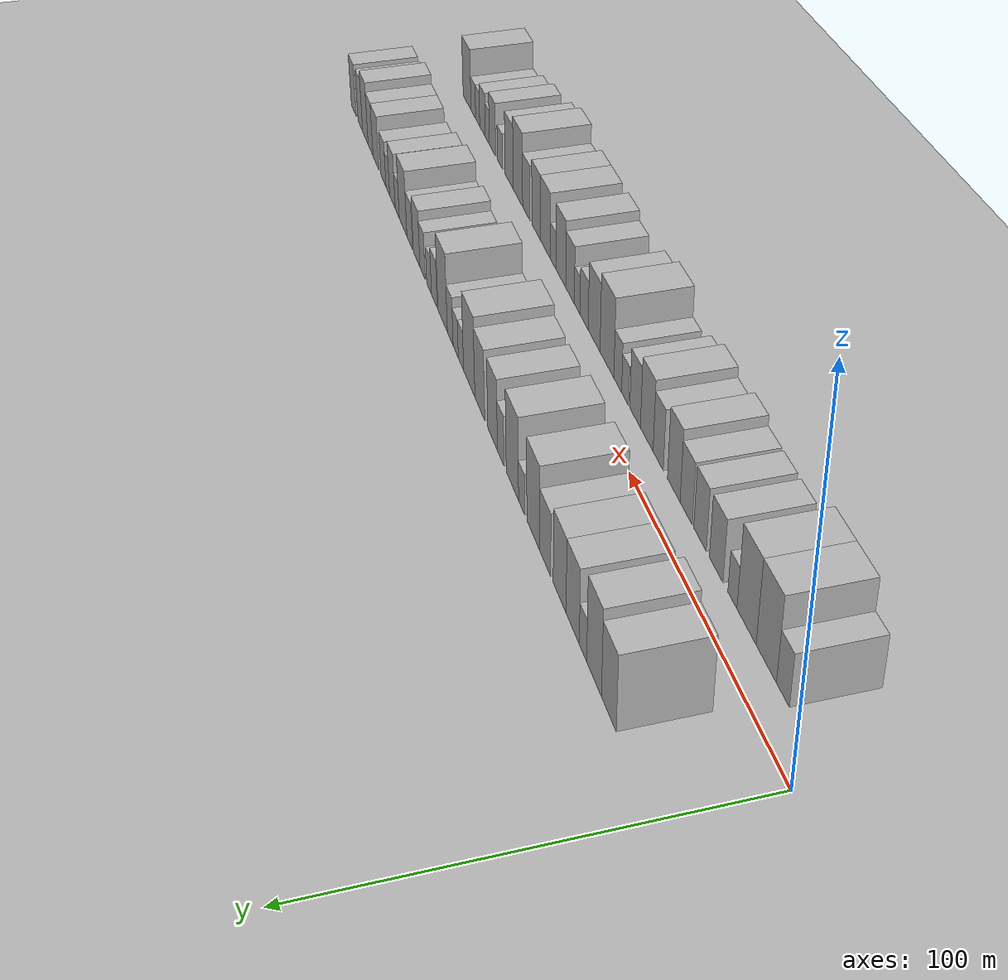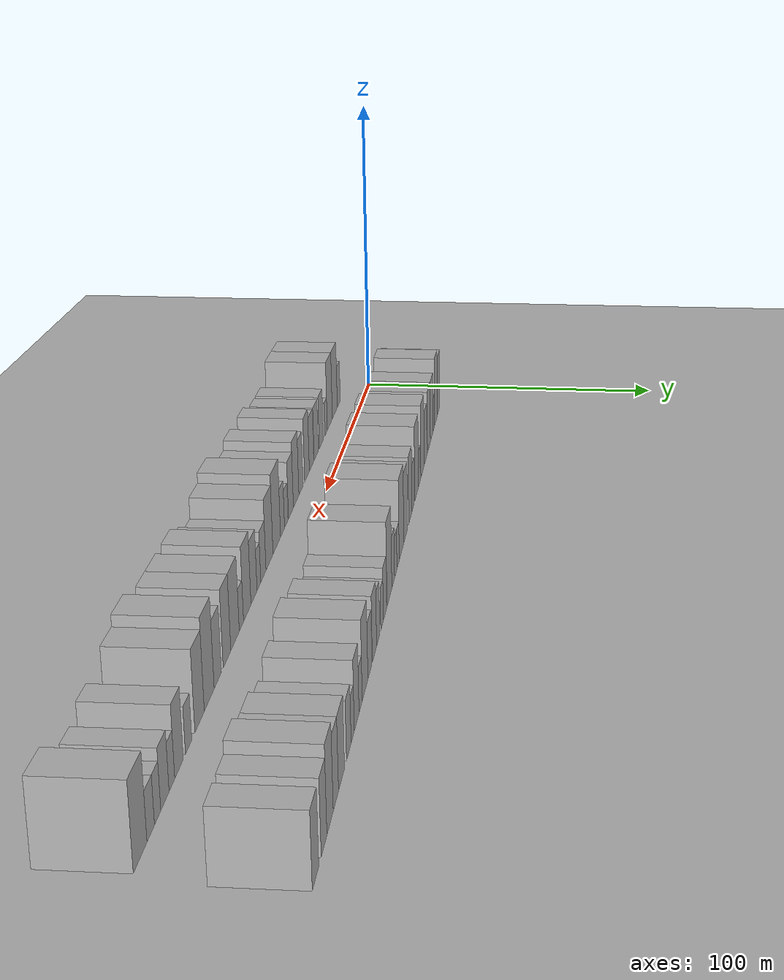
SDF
<?xml version="1.0" encoding="utf-8"?>

<sdf version="1.6">

   <world name="default">

      <gui fullscreen="0">

         <camera name="user_camera">

            <pose>-15 0 4.57585 0 0 0</pose>

            <view_controller>orbit</view_controller>

         </camera>

      </gui>

      <scene>

         <sky>

           <clouds>

             <speed>12</speed>

           </clouds>

         </sky>

         <ambient>0.4 0.4 0.4 1</ambient>

         <background>0.7 0.7 0.7 1</background>

         <shadows>1</shadows>

      </scene>

      <gravity>0 0 -9.8066</gravity>

      <magnetic_field>6e-06 2.3e-05 -4.2e-05</magnetic_field>

      <physics default="0" name="default_physics" type="ode">

         <ode>

            <solver>

               <type>quick</type>

               <iters>10</iters>

               <sor>1.0</sor>

               <use_dynamic_moi_rescaling>0</use_dynamic_moi_rescaling>

            </solver>

            <constraints>

               <cfm>0</cfm>

               <erp>0.2</erp>

               <contact_max_correcting_vel>100</contact_max_correcting_vel>

               <contact_surface_layer>0.001</contact_surface_layer>

            </constraints>

         </ode>

         <max_step_size>0.004</max_step_size>

         <real_time_factor>1</real_time_factor>

         <real_time_update_rate>250</real_time_update_rate>

      </physics>

      <light name="sun" type="directional">

         <cast_shadows>1</cast_shadows>

         <pose>0 0 10 0 0 0</pose>

         <diffuse>0.8 0.8 0.8 1</diffuse>

         <specular>0.2 0.2 0.2 1</specular>

         <attenuation>

            <range>1000</range>

            <constant>0.9</constant>

            <linear>0.01</linear>

            <quadratic>0.001</quadratic>

         </attenuation>

         <direction>-0.5 0.1 -0.9</direction>

      </light>

      <include>

         <name>ground_plane_1</name>

         <uri>model://HANNAS_ground_plane</uri>

         <pose>0 0 0  0 0 0</pose>

      </include>

      <include>

         <name>ground_plane_2</name>

         <uri>model://HANNAS_ground_plane</uri>

         <pose>100 0 0  0 0 0</pose>

      </include>

      <model name="building_1">

         <static>1</static>

         <pose frame="">27.9174 17.5000 0 0.000000 0.000000 1.570796</pose>

         <link name="link">

            <pose frame="">0 0 10.50 0 0 0</pose>

            <collision name="collision">

               <geometry>

                  <box>

                     <size>20.0000 9.8348 21.0000</size>

                  </box>

               </geometry>

               <max_contacts>10</max_contacts>

               <surface>

                  <contact>

                     <ode/>

                  </contact>

                  <bounce/>

                  <friction>

                     <torsional>

                        <ode/>

                     </torsional>

                     <ode/>

                  </friction>

               </surface>

            </collision>

            <visual name="visual">

               <cast_shadows>0</cast_shadows>

               <geometry>

                  <box>

                     <size>20.0000 9.8348 21.0000</size>

                  </box>

               </geometry>

               <material>

                  <script>

                     <uri>model://HANNAS_wall/materials/scripts</uri>

                     <uri>model://HANNAS_wall/materials/textures</uri>

                     <name>vrc/HANNAS_wall</name>

                  </script>

               </material>

            </visual>

            <self_collide>0</self_collide>

            <enable_wind>0</enable_wind>

            <kinematic>0</kinematic>

         </link>

      </model>

      <model name="building_2">

         <static>1</static>

         <pose frame="">37.9204 17.5000 0 0.000000 0.000000 1.570796</pose>

         <link name="link">

            <pose frame="">0 0 12.00 0 0 0</pose>

            <collision name="collision">

               <geometry>

                  <box>

                     <size>20.0000 10.1712 24.0000</size>

                  </box>

               </geometry>

               <max_contacts>10</max_contacts>

               <surface>

                  <contact>

                     <ode/>

                  </contact>

                  <bounce/>

                  <friction>

                     <torsional>

                        <ode/>

                     </torsional>

                     <ode/>

                  </friction>

               </surface>

            </collision>

            <visual name="visual">

               <cast_shadows>0</cast_shadows>

               <geometry>

                  <box>

                     <size>20.0000 10.1712 24.0000</size>

                  </box>

               </geometry>

               <material>

                  <script>

                     <uri>model://HANNAS_wall/materials/scripts</uri>

                     <uri>model://HANNAS_wall/materials/textures</uri>

                     <name>vrc/HANNAS_wall</name>

                  </script>

               </material>

            </visual>

            <self_collide>0</self_collide>

            <enable_wind>0</enable_wind>

            <kinematic>0</kinematic>

         </link>

      </model>

      <model name="building_3">

         <static>1</static>

         <pose frame="">45.6381 17.5000 0 0.000000 0.000000 1.570796</pose>

         <link name="link">

            <pose frame="">0 0 6.00 0 0 0</pose>

            <collision name="collision">

               <geometry>

                  <box>

                     <size>20.0000 5.2643 12.0000</size>

                  </box>

               </geometry>

               <max_contacts>10</max_contacts>

               <surface>

                  <contact>

                     <ode/>

                  </contact>

                  <bounce/>

                  <friction>

                     <torsional>

                        <ode/>

                     </torsional>

                     <ode/>

                  </friction>

               </surface>

            </collision>

            <visual name="visual">

               <cast_shadows>0</cast_shadows>

               <geometry>

                  <box>

                     <size>20.0000 5.2643 12.0000</size>

                  </box>

               </geometry>

               <material>

                  <script>

                     <uri>model://HANNAS_wall/materials/scripts</uri>

                     <uri>model://HANNAS_wall/materials/textures</uri>

                     <name>vrc/HANNAS_wall</name>

                  </script>

               </material>

            </visual>

            <self_collide>0</self_collide>

            <enable_wind>0</enable_wind>

            <kinematic>0</kinematic>

         </link>

      </model>

      <model name="building_4">

         <static>1</static>

         <pose frame="">53.1156 17.5000 0 0.000000 0.000000 1.570796</pose>

         <link name="link">

            <pose frame="">0 0 10.50 0 0 0</pose>

            <collision name="collision">

               <geometry>

                  <box>

                     <size>20.0000 9.6906 21.0000</size>

                  </box>

               </geometry>

               <max_contacts>10</max_contacts>

               <surface>

                  <contact>

                     <ode/>

                  </contact>

                  <bounce/>

                  <friction>

                     <torsional>

                        <ode/>

                     </torsional>

                     <ode/>

                  </friction>

               </surface>

            </collision>

            <visual name="visual">

               <cast_shadows>0</cast_shadows>

               <geometry>

                  <box>

                     <size>20.0000 9.6906 21.0000</size>

                  </box>

               </geometry>

               <material>

                  <script>

                     <uri>model://HANNAS_wall/materials/scripts</uri>

                     <uri>model://HANNAS_wall/materials/textures</uri>

                     <name>vrc/HANNAS_wall</name>

                  </script>

               </material>

            </visual>

            <self_collide>0</self_collide>

            <enable_wind>0</enable_wind>

            <kinematic>0</kinematic>

         </link>

      </model>

      <model name="building_5">

         <static>1</static>

         <pose frame="">62.9081 17.5000 0 0.000000 0.000000 1.570796</pose>

         <link name="link">

            <pose frame="">0 0 10.50 0 0 0</pose>

            <collision name="collision">

               <geometry>

                  <box>

                     <size>20.0000 9.8944 21.0000</size>

                  </box>

               </geometry>

               <max_contacts>10</max_contacts>

               <surface>

                  <contact>

                     <ode/>

                  </contact>

                  <bounce/>

                  <friction>

                     <torsional>

                        <ode/>

                     </torsional>

                     <ode/>

                  </friction>

               </surface>

            </collision>

            <visual name="visual">

               <cast_shadows>0</cast_shadows>

               <geometry>

                  <box>

                     <size>20.0000 9.8944 21.0000</size>

                  </box>

               </geometry>

               <material>

                  <script>

                     <uri>model://HANNAS_wall/materials/scripts</uri>

                     <uri>model://HANNAS_wall/materials/textures</uri>

                     <name>vrc/HANNAS_wall</name>

                  </script>

               </material>

            </visual>

            <self_collide>0</self_collide>

            <enable_wind>0</enable_wind>

            <kinematic>0</kinematic>

         </link>

      </model>

      <model name="building_6">

         <static>1</static>

         <pose frame="">74.2318 17.5000 0 0.000000 0.000000 1.570796</pose>

         <link name="link">

            <pose frame="">0 0 9.00 0 0 0</pose>

            <collision name="collision">

               <geometry>

                  <box>

                     <size>20.0000 8.7530 18.0000</size>

                  </box>

               </geometry>

               <max_contacts>10</max_contacts>

               <surface>

                  <contact>

                     <ode/>

                  </contact>

                  <bounce/>

                  <friction>

                     <torsional>

                        <ode/>

                     </torsional>

                     <ode/>

                  </friction>

               </surface>

            </collision>

            <visual name="visual">

               <cast_shadows>0</cast_shadows>

               <geometry>

                  <box>

                     <size>20.0000 8.7530 18.0000</size>

                  </box>

               </geometry>

               <material>

                  <script>

                     <uri>model://HANNAS_wall/materials/scripts</uri>

                     <uri>model://HANNAS_wall/materials/textures</uri>

                     <name>vrc/HANNAS_wall</name>

                  </script>

               </material>

            </visual>

            <self_collide>0</self_collide>

            <enable_wind>0</enable_wind>

            <kinematic>0</kinematic>

         </link>

      </model>

      <model name="building_7">

         <static>1</static>

         <pose frame="">83.9344 17.5000 0 0.000000 0.000000 1.570796</pose>

         <link name="link">

            <pose frame="">0 0 12.00 0 0 0</pose>

            <collision name="collision">

               <geometry>

                  <box>

                     <size>20.0000 10.6521 24.0000</size>

                  </box>

               </geometry>

               <max_contacts>10</max_contacts>

               <surface>

                  <contact>

                     <ode/>

                  </contact>

                  <bounce/>

                  <friction>

                     <torsional>

                        <ode/>

                     </torsional>

                     <ode/>

                  </friction>

               </surface>

            </collision>

            <visual name="visual">

               <cast_shadows>0</cast_shadows>

               <geometry>

                  <box>

                     <size>20.0000 10.6521 24.0000</size>

                  </box>

               </geometry>

               <material>

                  <script>

                     <uri>model://HANNAS_wall/materials/scripts</uri>

                     <uri>model://HANNAS_wall/materials/textures</uri>

                     <name>vrc/HANNAS_wall</name>

                  </script>

               </material>

            </visual>

            <self_collide>0</self_collide>

            <enable_wind>0</enable_wind>

            <kinematic>0</kinematic>

         </link>

      </model>

      <model name="building_8">

         <static>1</static>

         <pose frame="">93.8363 17.5000 0 0.000000 0.000000 1.570796</pose>

         <link name="link">

            <pose frame="">0 0 6.00 0 0 0</pose>

            <collision name="collision">

               <geometry>

                  <box>

                     <size>20.0000 5.1517 12.0000</size>

                  </box>

               </geometry>

               <max_contacts>10</max_contacts>

               <surface>

                  <contact>

                     <ode/>

                  </contact>

                  <bounce/>

                  <friction>

                     <torsional>

                        <ode/>

                     </torsional>

                     <ode/>

                  </friction>

               </surface>

            </collision>

            <visual name="visual">

               <cast_shadows>0</cast_shadows>

               <geometry>

                  <box>

                     <size>20.0000 5.1517 12.0000</size>

                  </box>

               </geometry>

               <material>

                  <script>

                     <uri>model://HANNAS_wall/materials/scripts</uri>

                     <uri>model://HANNAS_wall/materials/textures</uri>

                     <name>vrc/HANNAS_wall</name>

                  </script>

               </material>

            </visual>

            <self_collide>0</self_collide>

            <enable_wind>0</enable_wind>

            <kinematic>0</kinematic>

         </link>

      </model>

      <model name="building_9">

         <static>1</static>

         <pose frame="">101.9231 17.5000 0 0.000000 0.000000 1.570796</pose>

         <link name="link">

            <pose frame="">0 0 12.00 0 0 0</pose>

            <collision name="collision">

               <geometry>

                  <box>

                     <size>20.0000 11.0219 24.0000</size>

                  </box>

               </geometry>

               <max_contacts>10</max_contacts>

               <surface>

                  <contact>

                     <ode/>

                  </contact>

                  <bounce/>

                  <friction>

                     <torsional>

                        <ode/>

                     </torsional>

                     <ode/>

                  </friction>

               </surface>

            </collision>

            <visual name="visual">

               <cast_shadows>0</cast_shadows>

               <geometry>

                  <box>

                     <size>20.0000 11.0219 24.0000</size>

                  </box>

               </geometry>

               <material>

                  <script>

                     <uri>model://HANNAS_wall/materials/scripts</uri>

                     <uri>model://HANNAS_wall/materials/textures</uri>

                     <name>vrc/HANNAS_wall</name>

                  </script>

               </material>

            </visual>

            <self_collide>0</self_collide>

            <enable_wind>0</enable_wind>

            <kinematic>0</kinematic>

         </link>

      </model>

      <model name="building_10">

         <static>1</static>

         <pose frame="">112.4513 17.5000 0 0.000000 0.000000 1.570796</pose>

         <link name="link">

            <pose frame="">0 0 7.50 0 0 0</pose>

            <collision name="collision">

               <geometry>

                  <box>

                     <size>20.0000 6.0345 15.0000</size>

                  </box>

               </geometry>

               <max_contacts>10</max_contacts>

               <surface>

                  <contact>

                     <ode/>

                  </contact>

                  <bounce/>

                  <friction>

                     <torsional>

                        <ode/>

                     </torsional>

                     <ode/>

                  </friction>

               </surface>

            </collision>

            <visual name="visual">

               <cast_shadows>0</cast_shadows>

               <geometry>

                  <box>

                     <size>20.0000 6.0345 15.0000</size>

                  </box>

               </geometry>

               <material>

                  <script>

                     <uri>model://HANNAS_wall/materials/scripts</uri>

                     <uri>model://HANNAS_wall/materials/textures</uri>

                     <name>vrc/HANNAS_wall</name>

                  </script>

               </material>

            </visual>

            <self_collide>0</self_collide>

            <enable_wind>0</enable_wind>

            <kinematic>0</kinematic>

         </link>

      </model>

      <model name="building_11">

         <static>1</static>

         <pose frame="">120.0510 17.5000 0 0.000000 0.000000 1.570796</pose>

         <link name="link">

            <pose frame="">0 0 10.50 0 0 0</pose>

            <collision name="collision">

               <geometry>

                  <box>

                     <size>20.0000 9.1649 21.0000</size>

                  </box>

               </geometry>

               <max_contacts>10</max_contacts>

               <surface>

                  <contact>

                     <ode/>

                  </contact>

                  <bounce/>

                  <friction>

                     <torsional>

                        <ode/>

                     </torsional>

                     <ode/>

                  </friction>

               </surface>

            </collision>

            <visual name="visual">

               <cast_shadows>0</cast_shadows>

               <geometry>

                  <box>

                     <size>20.0000 9.1649 21.0000</size>

                  </box>

               </geometry>

               <material>

                  <script>

                     <uri>model://HANNAS_wall/materials/scripts</uri>

                     <uri>model://HANNAS_wall/materials/textures</uri>

                     <name>vrc/HANNAS_wall</name>

                  </script>

               </material>

            </visual>

            <self_collide>0</self_collide>

            <enable_wind>0</enable_wind>

            <kinematic>0</kinematic>

         </link>

      </model>

      <model name="building_12">

         <static>1</static>

         <pose frame="">132.5049 17.5000 0 0.000000 0.000000 1.570796</pose>

         <link name="link">

            <pose frame="">0 0 10.50 0 0 0</pose>

            <collision name="collision">

               <geometry>

                  <box>

                     <size>20.0000 9.7430 21.0000</size>

                  </box>

               </geometry>

               <max_contacts>10</max_contacts>

               <surface>

                  <contact>

                     <ode/>

                  </contact>

                  <bounce/>

                  <friction>

                     <torsional>

                        <ode/>

                     </torsional>

                     <ode/>

                  </friction>

               </surface>

            </collision>

            <visual name="visual">

               <cast_shadows>0</cast_shadows>

               <geometry>

                  <box>

                     <size>20.0000 9.7430 21.0000</size>

                  </box>

               </geometry>

               <material>

                  <script>

                     <uri>model://HANNAS_wall/materials/scripts</uri>

                     <uri>model://HANNAS_wall/materials/textures</uri>

                     <name>vrc/HANNAS_wall</name>

                  </script>

               </material>

            </visual>

            <self_collide>0</self_collide>

            <enable_wind>0</enable_wind>

            <kinematic>0</kinematic>

         </link>

      </model>

      <model name="building_13">

         <static>1</static>

         <pose frame="">143.2016 17.5000 0 0.000000 0.000000 1.570796</pose>

         <link name="link">

            <pose frame="">0 0 12.00 0 0 0</pose>

            <collision name="collision">

               <geometry>

                  <box>

                     <size>20.0000 11.6503 24.0000</size>

                  </box>

               </geometry>

               <max_contacts>10</max_contacts>

               <surface>

                  <contact>

                     <ode/>

                  </contact>

                  <bounce/>

                  <friction>

                     <torsional>

                        <ode/>

                     </torsional>

                     <ode/>

                  </friction>

               </surface>

            </collision>

            <visual name="visual">

               <cast_shadows>0</cast_shadows>

               <geometry>

                  <box>

                     <size>20.0000 11.6503 24.0000</size>

                  </box>

               </geometry>

               <material>

                  <script>

                     <uri>model://HANNAS_wall/materials/scripts</uri>

                     <uri>model://HANNAS_wall/materials/textures</uri>

                     <name>vrc/HANNAS_wall</name>

                  </script>

               </material>

            </visual>

            <self_collide>0</self_collide>

            <enable_wind>0</enable_wind>

            <kinematic>0</kinematic>

         </link>

      </model>

      <model name="building_14">

         <static>1</static>

         <pose frame="">151.8457 17.5000 0 0.000000 0.000000 1.570796</pose>

         <link name="link">

            <pose frame="">0 0 6.00 0 0 0</pose>

            <collision name="collision">

               <geometry>

                  <box>

                     <size>20.0000 5.6377 12.0000</size>

                  </box>

               </geometry>

               <max_contacts>10</max_contacts>

               <surface>

                  <contact>

                     <ode/>

                  </contact>

                  <bounce/>

                  <friction>

                     <torsional>

                        <ode/>

                     </torsional>

                     <ode/>

                  </friction>

               </surface>

            </collision>

            <visual name="visual">

               <cast_shadows>0</cast_shadows>

               <geometry>

                  <box>

                     <size>20.0000 5.6377 12.0000</size>

                  </box>

               </geometry>

               <material>

                  <script>

                     <uri>model://HANNAS_wall/materials/scripts</uri>

                     <uri>model://HANNAS_wall/materials/textures</uri>

                     <name>vrc/HANNAS_wall</name>

                  </script>

               </material>

            </visual>

            <self_collide>0</self_collide>

            <enable_wind>0</enable_wind>

            <kinematic>0</kinematic>

         </link>

      </model>

      <model name="building_15">

         <static>1</static>

         <pose frame="">157.4755 17.5000 0 0.000000 0.000000 1.570796</pose>

         <link name="link">

            <pose frame="">0 0 6.00 0 0 0</pose>

            <collision name="collision">

               <geometry>

                  <box>

                     <size>20.0000 5.6219 12.0000</size>

                  </box>

               </geometry>

               <max_contacts>10</max_contacts>

               <surface>

                  <contact>

                     <ode/>

                  </contact>

                  <bounce/>

                  <friction>

                     <torsional>

                        <ode/>

                     </torsional>

                     <ode/>

                  </friction>

               </surface>

            </collision>

            <visual name="visual">

               <cast_shadows>0</cast_shadows>

               <geometry>

                  <box>

                     <size>20.0000 5.6219 12.0000</size>

                  </box>

               </geometry>

               <material>

                  <script>

                     <uri>model://HANNAS_wall/materials/scripts</uri>

                     <uri>model://HANNAS_wall/materials/textures</uri>

                     <name>vrc/HANNAS_wall</name>

                  </script>

               </material>

            </visual>

            <self_collide>0</self_collide>

            <enable_wind>0</enable_wind>

            <kinematic>0</kinematic>

         </link>

      </model>

      <model name="building_16">

         <static>1</static>

         <pose frame="">163.4410 17.5000 0 0.000000 0.000000 1.570796</pose>

         <link name="link">

            <pose frame="">0 0 7.50 0 0 0</pose>

            <collision name="collision">

               <geometry>

                  <box>

                     <size>20.0000 6.3091 15.0000</size>

                  </box>

               </geometry>

               <max_contacts>10</max_contacts>

               <surface>

                  <contact>

                     <ode/>

                  </contact>

                  <bounce/>

                  <friction>

                     <torsional>

                        <ode/>

                     </torsional>

                     <ode/>

                  </friction>

               </surface>

            </collision>

            <visual name="visual">

               <cast_shadows>0</cast_shadows>

               <geometry>

                  <box>

                     <size>20.0000 6.3091 15.0000</size>

                  </box>

               </geometry>

               <material>

                  <script>

                     <uri>model://HANNAS_wall/materials/scripts</uri>

                     <uri>model://HANNAS_wall/materials/textures</uri>

                     <name>vrc/HANNAS_wall</name>

                  </script>

               </material>

            </visual>

            <self_collide>0</self_collide>

            <enable_wind>0</enable_wind>

            <kinematic>0</kinematic>

         </link>

      </model>

      <model name="building_17">

         <static>1</static>

         <pose frame="">171.9208 17.5000 0 0.000000 0.000000 1.570796</pose>

         <link name="link">

            <pose frame="">0 0 12.00 0 0 0</pose>

            <collision name="collision">

               <geometry>

                  <box>

                     <size>20.0000 10.6506 24.0000</size>

                  </box>

               </geometry>

               <max_contacts>10</max_contacts>

               <surface>

                  <contact>

                     <ode/>

                  </contact>

                  <bounce/>

                  <friction>

                     <torsional>

                        <ode/>

                     </torsional>

                     <ode/>

                  </friction>

               </surface>

            </collision>

            <visual name="visual">

               <cast_shadows>0</cast_shadows>

               <geometry>

                  <box>

                     <size>20.0000 10.6506 24.0000</size>

                  </box>

               </geometry>

               <material>

                  <script>

                     <uri>model://HANNAS_wall/materials/scripts</uri>

                     <uri>model://HANNAS_wall/materials/textures</uri>

                     <name>vrc/HANNAS_wall</name>

                  </script>

               </material>

            </visual>

            <self_collide>0</self_collide>

            <enable_wind>0</enable_wind>

            <kinematic>0</kinematic>

         </link>

      </model>

      <model name="building_18">

         <static>1</static>

         <pose frame="">181.5839 17.5000 0 0.000000 0.000000 1.570796</pose>

         <link name="link">

            <pose frame="">0 0 7.50 0 0 0</pose>

            <collision name="collision">

               <geometry>

                  <box>

                     <size>20.0000 6.6756 15.0000</size>

                  </box>

               </geometry>

               <max_contacts>10</max_contacts>

               <surface>

                  <contact>

                     <ode/>

                  </contact>

                  <bounce/>

                  <friction>

                     <torsional>

                        <ode/>

                     </torsional>

                     <ode/>

                  </friction>

               </surface>

            </collision>

            <visual name="visual">

               <cast_shadows>0</cast_shadows>

               <geometry>

                  <box>

                     <size>20.0000 6.6756 15.0000</size>

                  </box>

               </geometry>

               <material>

                  <script>

                     <uri>model://HANNAS_wall/materials/scripts</uri>

                     <uri>model://HANNAS_wall/materials/textures</uri>

                     <name>vrc/HANNAS_wall</name>

                  </script>

               </material>

            </visual>

            <self_collide>0</self_collide>

            <enable_wind>0</enable_wind>

            <kinematic>0</kinematic>

         </link>

      </model>

      <model name="building_19">

         <static>1</static>

         <pose frame="">187.7343 17.5000 0 0.000000 0.000000 1.570796</pose>

         <link name="link">

            <pose frame="">0 0 6.00 0 0 0</pose>

            <collision name="collision">

               <geometry>

                  <box>

                     <size>20.0000 5.6251 12.0000</size>

                  </box>

               </geometry>

               <max_contacts>10</max_contacts>

               <surface>

                  <contact>

                     <ode/>

                  </contact>

                  <bounce/>

                  <friction>

                     <torsional>

                        <ode/>

                     </torsional>

                     <ode/>

                  </friction>

               </surface>

            </collision>

            <visual name="visual">

               <cast_shadows>0</cast_shadows>

               <geometry>

                  <box>

                     <size>20.0000 5.6251 12.0000</size>

                  </box>

               </geometry>

               <material>

                  <script>

                     <uri>model://HANNAS_wall/materials/scripts</uri>

                     <uri>model://HANNAS_wall/materials/textures</uri>

                     <name>vrc/HANNAS_wall</name>

                  </script>

               </material>

            </visual>

            <self_collide>0</self_collide>

            <enable_wind>0</enable_wind>

            <kinematic>0</kinematic>

         </link>

      </model>

      <model name="building_20">

         <static>1</static>

         <pose frame="">195.6751 17.5000 0 0.000000 0.000000 1.570796</pose>

         <link name="link">

            <pose frame="">0 0 7.50 0 0 0</pose>

            <collision name="collision">

               <geometry>

                  <box>

                     <size>20.0000 6.2567 15.0000</size>

                  </box>

               </geometry>

               <max_contacts>10</max_contacts>

               <surface>

                  <contact>

                     <ode/>

                  </contact>

                  <bounce/>

                  <friction>

                     <torsional>

                        <ode/>

                     </torsional>

                     <ode/>

                  </friction>

               </surface>

            </collision>

            <visual name="visual">

               <cast_shadows>0</cast_shadows>

               <geometry>

                  <box>

                     <size>20.0000 6.2567 15.0000</size>

                  </box>

               </geometry>

               <material>

                  <script>

                     <uri>model://HANNAS_wall/materials/scripts</uri>

                     <uri>model://HANNAS_wall/materials/textures</uri>

                     <name>vrc/HANNAS_wall</name>

                  </script>

               </material>

            </visual>

            <self_collide>0</self_collide>

            <enable_wind>0</enable_wind>

            <kinematic>0</kinematic>

         </link>

      </model>

      <model name="building_21">

         <static>1</static>

         <pose frame="">202.9608 17.5000 0 0.000000 0.000000 1.570796</pose>

         <link name="link">

            <pose frame="">0 0 9.00 0 0 0</pose>

            <collision name="collision">

               <geometry>

                  <box>

                     <size>20.0000 8.3146 18.0000</size>

                  </box>

               </geometry>

               <max_contacts>10</max_contacts>

               <surface>

                  <contact>

                     <ode/>

                  </contact>

                  <bounce/>

                  <friction>

                     <torsional>

                        <ode/>

                     </torsional>

                     <ode/>

                  </friction>

               </surface>

            </collision>

            <visual name="visual">

               <cast_shadows>0</cast_shadows>

               <geometry>

                  <box>

                     <size>20.0000 8.3146 18.0000</size>

                  </box>

               </geometry>

               <material>

                  <script>

                     <uri>model://HANNAS_wall/materials/scripts</uri>

                     <uri>model://HANNAS_wall/materials/textures</uri>

                     <name>vrc/HANNAS_wall</name>

                  </script>

               </material>

            </visual>

            <self_collide>0</self_collide>

            <enable_wind>0</enable_wind>

            <kinematic>0</kinematic>

         </link>

      </model>

      <model name="building_22">

         <static>1</static>

         <pose frame="">211.7197 17.5000 0 0.000000 0.000000 1.570796</pose>

         <link name="link">

            <pose frame="">0 0 7.50 0 0 0</pose>

            <collision name="collision">

               <geometry>

                  <box>

                     <size>20.0000 7.2033 15.0000</size>

                  </box>

               </geometry>

               <max_contacts>10</max_contacts>

               <surface>

                  <contact>

                     <ode/>

                  </contact>

                  <bounce/>

                  <friction>

                     <torsional>

                        <ode/>

                     </torsional>

                     <ode/>

                  </friction>

               </surface>

            </collision>

            <visual name="visual">

               <cast_shadows>0</cast_shadows>

               <geometry>

                  <box>

                     <size>20.0000 7.2033 15.0000</size>

                  </box>

               </geometry>

               <material>

                  <script>

                     <uri>model://HANNAS_wall/materials/scripts</uri>

                     <uri>model://HANNAS_wall/materials/textures</uri>

                     <name>vrc/HANNAS_wall</name>

                  </script>

               </material>

            </visual>

            <self_collide>0</self_collide>

            <enable_wind>0</enable_wind>

            <kinematic>0</kinematic>

         </link>

      </model>

      <model name="building_23">

         <static>1</static>

         <pose frame="">220.3678 17.5000 0 0.000000 0.000000 1.570796</pose>

         <link name="link">

            <pose frame="">0 0 10.50 0 0 0</pose>

            <collision name="collision">

               <geometry>

                  <box>

                     <size>20.0000 10.0928 21.0000</size>

                  </box>

               </geometry>

               <max_contacts>10</max_contacts>

               <surface>

                  <contact>

                     <ode/>

                  </contact>

                  <bounce/>

                  <friction>

                     <torsional>

                        <ode/>

                     </torsional>

                     <ode/>

                  </friction>

               </surface>

            </collision>

            <visual name="visual">

               <cast_shadows>0</cast_shadows>

               <geometry>

                  <box>

                     <size>20.0000 10.0928 21.0000</size>

                  </box>

               </geometry>

               <material>

                  <script>

                     <uri>model://HANNAS_wall/materials/scripts</uri>

                     <uri>model://HANNAS_wall/materials/textures</uri>

                     <name>vrc/HANNAS_wall</name>

                  </script>

               </material>

            </visual>

            <self_collide>0</self_collide>

            <enable_wind>0</enable_wind>

            <kinematic>0</kinematic>

         </link>

      </model>

      <model name="building_24">

         <static>1</static>

         <pose frame="">228.1583 17.5000 0 0.000000 0.000000 1.570796</pose>

         <link name="link">

            <pose frame="">0 0 6.00 0 0 0</pose>

            <collision name="collision">

               <geometry>

                  <box>

                     <size>20.0000 5.4883 12.0000</size>

                  </box>

               </geometry>

               <max_contacts>10</max_contacts>

               <surface>

                  <contact>

                     <ode/>

                  </contact>

                  <bounce/>

                  <friction>

                     <torsional>

                        <ode/>

                     </torsional>

                     <ode/>

                  </friction>

               </surface>

            </collision>

            <visual name="visual">

               <cast_shadows>0</cast_shadows>

               <geometry>

                  <box>

                     <size>20.0000 5.4883 12.0000</size>

                  </box>

               </geometry>

               <material>

                  <script>

                     <uri>model://HANNAS_wall/materials/scripts</uri>

                     <uri>model://HANNAS_wall/materials/textures</uri>

                     <name>vrc/HANNAS_wall</name>

                  </script>

               </material>

            </visual>

            <self_collide>0</self_collide>

            <enable_wind>0</enable_wind>

            <kinematic>0</kinematic>

         </link>

      </model>

      <model name="building_25">

         <static>1</static>

         <pose frame="">234.7926 17.5000 0 0.000000 0.000000 1.570796</pose>

         <link name="link">

            <pose frame="">0 0 9.00 0 0 0</pose>

            <collision name="collision">

               <geometry>

                  <box>

                     <size>20.0000 7.7801 18.0000</size>

                  </box>

               </geometry>

               <max_contacts>10</max_contacts>

               <surface>

                  <contact>

                     <ode/>

                  </contact>

                  <bounce/>

                  <friction>

                     <torsional>

                        <ode/>

                     </torsional>

                     <ode/>

                  </friction>

               </surface>

            </collision>

            <visual name="visual">

               <cast_shadows>0</cast_shadows>

               <geometry>

                  <box>

                     <size>20.0000 7.7801 18.0000</size>

                  </box>

               </geometry>

               <material>

                  <script>

                     <uri>model://HANNAS_wall/materials/scripts</uri>

                     <uri>model://HANNAS_wall/materials/textures</uri>

                     <name>vrc/HANNAS_wall</name>

                  </script>

               </material>

            </visual>

            <self_collide>0</self_collide>

            <enable_wind>0</enable_wind>

            <kinematic>0</kinematic>

         </link>

      </model>

      <model name="building_26">

         <static>1</static>

         <pose frame="">241.2350 17.5000 0 0.000000 0.000000 1.570796</pose>

         <link name="link">

            <pose frame="">0 0 6.00 0 0 0</pose>

            <collision name="collision">

               <geometry>

                  <box>

                     <size>20.0000 5.1048 12.0000</size>

                  </box>

               </geometry>

               <max_contacts>10</max_contacts>

               <surface>

                  <contact>

                     <ode/>

                  </contact>

                  <bounce/>

                  <friction>

                     <torsional>

                        <ode/>

                     </torsional>

                     <ode/>

                  </friction>

               </surface>

            </collision>

            <visual name="visual">

               <cast_shadows>0</cast_shadows>

               <geometry>

                  <box>

                     <size>20.0000 5.1048 12.0000</size>

                  </box>

               </geometry>

               <material>

                  <script>

                     <uri>model://HANNAS_wall/materials/scripts</uri>

                     <uri>model://HANNAS_wall/materials/textures</uri>

                     <name>vrc/HANNAS_wall</name>

                  </script>

               </material>

            </visual>

            <self_collide>0</self_collide>

            <enable_wind>0</enable_wind>

            <kinematic>0</kinematic>

         </link>

      </model>

      <model name="building_27">

         <static>1</static>

         <pose frame="">247.3665 17.5000 0 0.000000 0.000000 1.570796</pose>

         <link name="link">

            <pose frame="">0 0 7.50 0 0 0</pose>

            <collision name="collision">

               <geometry>

                  <box>

                     <size>20.0000 7.1582 15.0000</size>

                  </box>

               </geometry>

               <max_contacts>10</max_contacts>

               <surface>

                  <contact>

                     <ode/>

                  </contact>

                  <bounce/>

                  <friction>

                     <torsional>

                        <ode/>

                     </torsional>

                     <ode/>

                  </friction>

               </surface>

            </collision>

            <visual name="visual">

               <cast_shadows>0</cast_shadows>

               <geometry>

                  <box>

                     <size>20.0000 7.1582 15.0000</size>

                  </box>

               </geometry>

               <material>

                  <script>

                     <uri>model://HANNAS_wall/materials/scripts</uri>

                     <uri>model://HANNAS_wall/materials/textures</uri>

                     <name>vrc/HANNAS_wall</name>

                  </script>

               </material>

            </visual>

            <self_collide>0</self_collide>

            <enable_wind>0</enable_wind>

            <kinematic>0</kinematic>

         </link>

      </model>

      <model name="building_28">

         <static>1</static>

         <pose frame="">258.2978 17.5000 0 0.000000 0.000000 1.570796</pose>

         <link name="link">

            <pose frame="">0 0 9.00 0 0 0</pose>

            <collision name="collision">

               <geometry>

                  <box>

                     <size>20.0000 8.7044 18.0000</size>

                  </box>

               </geometry>

               <max_contacts>10</max_contacts>

               <surface>

                  <contact>

                     <ode/>

                  </contact>

                  <bounce/>

                  <friction>

                     <torsional>

                        <ode/>

                     </torsional>

                     <ode/>

                  </friction>

               </surface>

            </collision>

            <visual name="visual">

               <cast_shadows>0</cast_shadows>

               <geometry>

                  <box>

                     <size>20.0000 8.7044 18.0000</size>

                  </box>

               </geometry>

               <material>

                  <script>

                     <uri>model://HANNAS_wall/materials/scripts</uri>

                     <uri>model://HANNAS_wall/materials/textures</uri>

                     <name>vrc/HANNAS_wall</name>

                  </script>

               </material>

            </visual>

            <self_collide>0</self_collide>

            <enable_wind>0</enable_wind>

            <kinematic>0</kinematic>

         </link>

      </model>

      <model name="building_29">

         <static>1</static>

         <pose frame="">266.3484 17.5000 0 0.000000 0.000000 1.570796</pose>

         <link name="link">

            <pose frame="">0 0 9.00 0 0 0</pose>

            <collision name="collision">

               <geometry>

                  <box>

                     <size>20.0000 7.3968 18.0000</size>

                  </box>

               </geometry>

               <max_contacts>10</max_contacts>

               <surface>

                  <contact>

                     <ode/>

                  </contact>

                  <bounce/>

                  <friction>

                     <torsional>

                        <ode/>

                     </torsional>

                     <ode/>

                  </friction>

               </surface>

            </collision>

            <visual name="visual">

               <cast_shadows>0</cast_shadows>

               <geometry>

                  <box>

                     <size>20.0000 7.3968 18.0000</size>

                  </box>

               </geometry>

               <material>

                  <script>

                     <uri>model://HANNAS_wall/materials/scripts</uri>

                     <uri>model://HANNAS_wall/materials/textures</uri>

                     <name>vrc/HANNAS_wall</name>

                  </script>

               </material>

            </visual>

            <self_collide>0</self_collide>

            <enable_wind>0</enable_wind>

            <kinematic>0</kinematic>

         </link>

      </model>

      <model name="building_30">

         <static>1</static>

         <pose frame="">274.2600 17.5000 0 0.000000 0.000000 1.570796</pose>

         <link name="link">

            <pose frame="">0 0 10.50 0 0 0</pose>

            <collision name="collision">

               <geometry>

                  <box>

                     <size>20.0000 8.4264 21.0000</size>

                  </box>

               </geometry>

               <max_contacts>10</max_contacts>

               <surface>

                  <contact>

                     <ode/>

                  </contact>

                  <bounce/>

                  <friction>

                     <torsional>

                        <ode/>

                     </torsional>

                     <ode/>

                  </friction>

               </surface>

            </collision>

            <visual name="visual">

               <cast_shadows>0</cast_shadows>

               <geometry>

                  <box>

                     <size>20.0000 8.4264 21.0000</size>

                  </box>

               </geometry>

               <material>

                  <script>

                     <uri>model://HANNAS_wall/materials/scripts</uri>

                     <uri>model://HANNAS_wall/materials/textures</uri>

                     <name>vrc/HANNAS_wall</name>

                  </script>

               </material>

            </visual>

            <self_collide>0</self_collide>

            <enable_wind>0</enable_wind>

            <kinematic>0</kinematic>

         </link>

      </model>

      <model name="building_31">

         <static>1</static>

         <pose frame="">282.1280 17.5000 0 0.000000 0.000000 1.570796</pose>

         <link name="link">

            <pose frame="">0 0 9.00 0 0 0</pose>

            <collision name="collision">

               <geometry>

                  <box>

                     <size>20.0000 7.3095 18.0000</size>

                  </box>

               </geometry>

               <max_contacts>10</max_contacts>

               <surface>

                  <contact>

                     <ode/>

                  </contact>

                  <bounce/>

                  <friction>

                     <torsional>

                        <ode/>

                     </torsional>

                     <ode/>

                  </friction>

               </surface>

            </collision>

            <visual name="visual">

               <cast_shadows>0</cast_shadows>

               <geometry>

                  <box>

                     <size>20.0000 7.3095 18.0000</size>

                  </box>

               </geometry>

               <material>

                  <script>

                     <uri>model://HANNAS_wall/materials/scripts</uri>

                     <uri>model://HANNAS_wall/materials/textures</uri>

                     <name>vrc/HANNAS_wall</name>

                  </script>

               </material>

            </visual>

            <self_collide>0</self_collide>

            <enable_wind>0</enable_wind>

            <kinematic>0</kinematic>

         </link>

      </model>

      <model name="building_32">

         <static>1</static>

         <pose frame="">292.6877 17.5000 0 0.000000 0.000000 1.570796</pose>

         <link name="link">

            <pose frame="">0 0 9.00 0 0 0</pose>

            <collision name="collision">

               <geometry>

                  <box>

                     <size>20.0000 7.8099 18.0000</size>

                  </box>

               </geometry>

               <max_contacts>10</max_contacts>

               <surface>

                  <contact>

                     <ode/>

                  </contact>

                  <bounce/>

                  <friction>

                     <torsional>

                        <ode/>

                     </torsional>

                     <ode/>

                  </friction>

               </surface>

            </collision>

            <visual name="visual">

               <cast_shadows>0</cast_shadows>

               <geometry>

                  <box>

                     <size>20.0000 7.8099 18.0000</size>

                  </box>

               </geometry>

               <material>

                  <script>

                     <uri>model://HANNAS_wall/materials/scripts</uri>

                     <uri>model://HANNAS_wall/materials/textures</uri>

                     <name>vrc/HANNAS_wall</name>

                  </script>

               </material>

            </visual>

            <self_collide>0</self_collide>

            <enable_wind>0</enable_wind>

            <kinematic>0</kinematic>

         </link>

      </model>

      <model name="building_33">

         <static>1</static>

         <pose frame="">23.4908 -17.5000 0 0.000000 0.000000 1.570796</pose>

         <link name="link">

            <pose frame="">0 0 7.50 0 0 0</pose>

            <collision name="collision">

               <geometry>

                  <box>

                     <size>20.0000 6.9815 15.0000</size>

                  </box>

               </geometry>

               <max_contacts>10</max_contacts>

               <surface>

                  <contact>

                     <ode/>

                  </contact>

                  <bounce/>

                  <friction>

                     <torsional>

                        <ode/>

                     </torsional>

                     <ode/>

                  </friction>

               </surface>

            </collision>

            <visual name="visual">

               <cast_shadows>0</cast_shadows>

               <geometry>

                  <box>

                     <size>20.0000 6.9815 15.0000</size>

                  </box>

               </geometry>

               <material>

                  <script>

                     <uri>model://HANNAS_wall/materials/scripts</uri>

                     <uri>model://HANNAS_wall/materials/textures</uri>

                     <name>vrc/HANNAS_wall</name>

                  </script>

               </material>

            </visual>

            <self_collide>0</self_collide>

            <enable_wind>0</enable_wind>

            <kinematic>0</kinematic>

         </link>

      </model>

      <model name="building_34">

         <static>1</static>

         <pose frame="">32.6551 -17.5000 0 0.000000 0.000000 1.570796</pose>

         <link name="link">

            <pose frame="">0 0 12.00 0 0 0</pose>

            <collision name="collision">

               <geometry>

                  <box>

                     <size>20.0000 11.3472 24.0000</size>

                  </box>

               </geometry>

               <max_contacts>10</max_contacts>

               <surface>

                  <contact>

                     <ode/>

                  </contact>

                  <bounce/>

                  <friction>

                     <torsional>

                        <ode/>

                     </torsional>

                     <ode/>

                  </friction>

               </surface>

            </collision>

            <visual name="visual">

               <cast_shadows>0</cast_shadows>

               <geometry>

                  <box>

                     <size>20.0000 11.3472 24.0000</size>

                  </box>

               </geometry>

               <material>

                  <script>

                     <uri>model://HANNAS_wall/materials/scripts</uri>

                     <uri>model://HANNAS_wall/materials/textures</uri>

                     <name>vrc/HANNAS_wall</name>

                  </script>

               </material>

            </visual>

            <self_collide>0</self_collide>

            <enable_wind>0</enable_wind>

            <kinematic>0</kinematic>

         </link>

      </model>

      <model name="building_35">

         <static>1</static>

         <pose frame="">43.9416 -17.5000 0 0.000000 0.000000 1.570796</pose>

         <link name="link">

            <pose frame="">0 0 12.00 0 0 0</pose>

            <collision name="collision">

               <geometry>

                  <box>

                     <size>20.0000 11.2258 24.0000</size>

                  </box>

               </geometry>

               <max_contacts>10</max_contacts>

               <surface>

                  <contact>

                     <ode/>

                  </contact>

                  <bounce/>

                  <friction>

                     <torsional>

                        <ode/>

                     </torsional>

                     <ode/>

                  </friction>

               </surface>

            </collision>

            <visual name="visual">

               <cast_shadows>0</cast_shadows>

               <geometry>

                  <box>

                     <size>20.0000 11.2258 24.0000</size>

                  </box>

               </geometry>

               <material>

                  <script>

                     <uri>model://HANNAS_wall/materials/scripts</uri>

                     <uri>model://HANNAS_wall/materials/textures</uri>

                     <name>vrc/HANNAS_wall</name>

                  </script>

               </material>

            </visual>

            <self_collide>0</self_collide>

            <enable_wind>0</enable_wind>

            <kinematic>0</kinematic>

         </link>

      </model>

      <model name="building_36">

         <static>1</static>

         <pose frame="">52.3091 -17.5000 0 0.000000 0.000000 1.570796</pose>

         <link name="link">

            <pose frame="">0 0 6.00 0 0 0</pose>

            <collision name="collision">

               <geometry>

                  <box>

                     <size>20.0000 5.5093 12.0000</size>

                  </box>

               </geometry>

               <max_contacts>10</max_contacts>

               <surface>

                  <contact>

                     <ode/>

                  </contact>

                  <bounce/>

                  <friction>

                     <torsional>

                        <ode/>

                     </torsional>

                     <ode/>

                  </friction>

               </surface>

            </collision>

            <visual name="visual">

               <cast_shadows>0</cast_shadows>

               <geometry>

                  <box>

                     <size>20.0000 5.5093 12.0000</size>

                  </box>

               </geometry>

               <material>

                  <script>

                     <uri>model://HANNAS_wall/materials/scripts</uri>

                     <uri>model://HANNAS_wall/materials/textures</uri>

                     <name>vrc/HANNAS_wall</name>

                  </script>

               </material>

            </visual>

            <self_collide>0</self_collide>

            <enable_wind>0</enable_wind>

            <kinematic>0</kinematic>

         </link>

      </model>

      <model name="building_37">

         <static>1</static>

         <pose frame="">62.3523 -17.5000 0 0.000000 0.000000 1.570796</pose>

         <link name="link">

            <pose frame="">0 0 9.00 0 0 0</pose>

            <collision name="collision">

               <geometry>

                  <box>

                     <size>20.0000 8.5772 18.0000</size>

                  </box>

               </geometry>

               <max_contacts>10</max_contacts>

               <surface>

                  <contact>

                     <ode/>

                  </contact>

                  <bounce/>

                  <friction>

                     <torsional>

                        <ode/>

                     </torsional>

                     <ode/>

                  </friction>

               </surface>

            </collision>

            <visual name="visual">

               <cast_shadows>0</cast_shadows>

               <geometry>

                  <box>

                     <size>20.0000 8.5772 18.0000</size>

                  </box>

               </geometry>

               <material>

                  <script>

                     <uri>model://HANNAS_wall/materials/scripts</uri>

                     <uri>model://HANNAS_wall/materials/textures</uri>

                     <name>vrc/HANNAS_wall</name>

                  </script>

               </material>

            </visual>

            <self_collide>0</self_collide>

            <enable_wind>0</enable_wind>

            <kinematic>0</kinematic>

         </link>

      </model>

      <model name="building_38">

         <static>1</static>

         <pose frame="">72.7440 -17.5000 0 0.000000 0.000000 1.570796</pose>

         <link name="link">

            <pose frame="">0 0 9.00 0 0 0</pose>

            <collision name="collision">

               <geometry>

                  <box>

                     <size>20.0000 8.2061 18.0000</size>

                  </box>

               </geometry>

               <max_contacts>10</max_contacts>

               <surface>

                  <contact>

                     <ode/>

                  </contact>

                  <bounce/>

                  <friction>

                     <torsional>

                        <ode/>

                     </torsional>

                     <ode/>

                  </friction>

               </surface>

            </collision>

            <visual name="visual">

               <cast_shadows>0</cast_shadows>

               <geometry>

                  <box>

                     <size>20.0000 8.2061 18.0000</size>

                  </box>

               </geometry>

               <material>

                  <script>

                     <uri>model://HANNAS_wall/materials/scripts</uri>

                     <uri>model://HANNAS_wall/materials/textures</uri>

                     <name>vrc/HANNAS_wall</name>

                  </script>

               </material>

            </visual>

            <self_collide>0</self_collide>

            <enable_wind>0</enable_wind>

            <kinematic>0</kinematic>

         </link>

      </model>

      <model name="building_39">

         <static>1</static>

         <pose frame="">81.9898 -17.5000 0 0.000000 0.000000 1.570796</pose>

         <link name="link">

            <pose frame="">0 0 9.00 0 0 0</pose>

            <collision name="collision">

               <geometry>

                  <box>

                     <size>20.0000 8.2856 18.0000</size>

                  </box>

               </geometry>

               <max_contacts>10</max_contacts>

               <surface>

                  <contact>

                     <ode/>

                  </contact>

                  <bounce/>

                  <friction>

                     <torsional>

                        <ode/>

                     </torsional>

                     <ode/>

                  </friction>

               </surface>

            </collision>

            <visual name="visual">

               <cast_shadows>0</cast_shadows>

               <geometry>

                  <box>

                     <size>20.0000 8.2856 18.0000</size>

                  </box>

               </geometry>

               <material>

                  <script>

                     <uri>model://HANNAS_wall/materials/scripts</uri>

                     <uri>model://HANNAS_wall/materials/textures</uri>

                     <name>vrc/HANNAS_wall</name>

                  </script>

               </material>

            </visual>

            <self_collide>0</self_collide>

            <enable_wind>0</enable_wind>

            <kinematic>0</kinematic>

         </link>

      </model>

      <model name="building_40">

         <static>1</static>

         <pose frame="">90.5377 -17.5000 0 0.000000 0.000000 1.570796</pose>

         <link name="link">

            <pose frame="">0 0 10.50 0 0 0</pose>

            <collision name="collision">

               <geometry>

                  <box>

                     <size>20.0000 8.8101 21.0000</size>

                  </box>

               </geometry>

               <max_contacts>10</max_contacts>

               <surface>

                  <contact>

                     <ode/>

                  </contact>

                  <bounce/>

                  <friction>

                     <torsional>

                        <ode/>

                     </torsional>

                     <ode/>

                  </friction>

               </surface>

            </collision>

            <visual name="visual">

               <cast_shadows>0</cast_shadows>

               <geometry>

                  <box>

                     <size>20.0000 8.8101 21.0000</size>

                  </box>

               </geometry>

               <material>

                  <script>

                     <uri>model://HANNAS_wall/materials/scripts</uri>

                     <uri>model://HANNAS_wall/materials/textures</uri>

                     <name>vrc/HANNAS_wall</name>

                  </script>

               </material>

            </visual>

            <self_collide>0</self_collide>

            <enable_wind>0</enable_wind>

            <kinematic>0</kinematic>

         </link>

      </model>

      <model name="building_41">

         <static>1</static>

         <pose frame="">101.6637 -17.5000 0 0.000000 0.000000 1.570796</pose>

         <link name="link">

            <pose frame="">0 0 9.00 0 0 0</pose>

            <collision name="collision">

               <geometry>

                  <box>

                     <size>20.0000 7.4419 18.0000</size>

                  </box>

               </geometry>

               <max_contacts>10</max_contacts>

               <surface>

                  <contact>

                     <ode/>

                  </contact>

                  <bounce/>

                  <friction>

                     <torsional>

                        <ode/>

                     </torsional>

                     <ode/>

                  </friction>

               </surface>

            </collision>

            <visual name="visual">

               <cast_shadows>0</cast_shadows>

               <geometry>

                  <box>

                     <size>20.0000 7.4419 18.0000</size>

                  </box>

               </geometry>

               <material>

                  <script>

                     <uri>model://HANNAS_wall/materials/scripts</uri>

                     <uri>model://HANNAS_wall/materials/textures</uri>

                     <name>vrc/HANNAS_wall</name>

                  </script>

               </material>

            </visual>

            <self_collide>0</self_collide>

            <enable_wind>0</enable_wind>

            <kinematic>0</kinematic>

         </link>

      </model>

      <model name="building_42">

         <static>1</static>

         <pose frame="">110.1735 -17.5000 0 0.000000 0.000000 1.570796</pose>

         <link name="link">

            <pose frame="">0 0 10.50 0 0 0</pose>

            <collision name="collision">

               <geometry>

                  <box>

                     <size>20.0000 9.5776 21.0000</size>

                  </box>

               </geometry>

               <max_contacts>10</max_contacts>

               <surface>

                  <contact>

                     <ode/>

                  </contact>

                  <bounce/>

                  <friction>

                     <torsional>

                        <ode/>

                     </torsional>

                     <ode/>

                  </friction>

               </surface>

            </collision>

            <visual name="visual">

               <cast_shadows>0</cast_shadows>

               <geometry>

                  <box>

                     <size>20.0000 9.5776 21.0000</size>

                  </box>

               </geometry>

               <material>

                  <script>

                     <uri>model://HANNAS_wall/materials/scripts</uri>

                     <uri>model://HANNAS_wall/materials/textures</uri>

                     <name>vrc/HANNAS_wall</name>

                  </script>

               </material>

            </visual>

            <self_collide>0</self_collide>

            <enable_wind>0</enable_wind>

            <kinematic>0</kinematic>

         </link>

      </model>

      <model name="building_43">

         <static>1</static>

         <pose frame="">119.0694 -17.5000 0 0.000000 0.000000 1.570796</pose>

         <link name="link">

            <pose frame="">0 0 9.00 0 0 0</pose>

            <collision name="collision">

               <geometry>

                  <box>

                     <size>20.0000 8.2141 18.0000</size>

                  </box>

               </geometry>

               <max_contacts>10</max_contacts>

               <surface>

                  <contact>

                     <ode/>

                  </contact>

                  <bounce/>

                  <friction>

                     <torsional>

                        <ode/>

                     </torsional>

                     <ode/>

                  </friction>

               </surface>

            </collision>

            <visual name="visual">

               <cast_shadows>0</cast_shadows>

               <geometry>

                  <box>

                     <size>20.0000 8.2141 18.0000</size>

                  </box>

               </geometry>

               <material>

                  <script>

                     <uri>model://HANNAS_wall/materials/scripts</uri>

                     <uri>model://HANNAS_wall/materials/textures</uri>

                     <name>vrc/HANNAS_wall</name>

                  </script>

               </material>

            </visual>

            <self_collide>0</self_collide>

            <enable_wind>0</enable_wind>

            <kinematic>0</kinematic>

         </link>

      </model>

      <model name="building_44">

         <static>1</static>

         <pose frame="">126.9564 -17.5000 0 0.000000 0.000000 1.570796</pose>

         <link name="link">

            <pose frame="">0 0 6.00 0 0 0</pose>

            <collision name="collision">

               <geometry>

                  <box>

                     <size>20.0000 5.5599 12.0000</size>

                  </box>

               </geometry>

               <max_contacts>10</max_contacts>

               <surface>

                  <contact>

                     <ode/>

                  </contact>

                  <bounce/>

                  <friction>

                     <torsional>

                        <ode/>

                     </torsional>

                     <ode/>

                  </friction>

               </surface>

            </collision>

            <visual name="visual">

               <cast_shadows>0</cast_shadows>

               <geometry>

                  <box>

                     <size>20.0000 5.5599 12.0000</size>

                  </box>

               </geometry>

               <material>

                  <script>

                     <uri>model://HANNAS_wall/materials/scripts</uri>

                     <uri>model://HANNAS_wall/materials/textures</uri>

                     <name>vrc/HANNAS_wall</name>

                  </script>

               </material>

            </visual>

            <self_collide>0</self_collide>

            <enable_wind>0</enable_wind>

            <kinematic>0</kinematic>

         </link>

      </model>

      <model name="building_45">

         <static>1</static>

         <pose frame="">132.8987 -17.5000 0 0.000000 0.000000 1.570796</pose>

         <link name="link">

            <pose frame="">0 0 7.50 0 0 0</pose>

            <collision name="collision">

               <geometry>

                  <box>

                     <size>20.0000 6.3248 15.0000</size>

                  </box>

               </geometry>

               <max_contacts>10</max_contacts>

               <surface>

                  <contact>

                     <ode/>

                  </contact>

                  <bounce/>

                  <friction>

                     <torsional>

                        <ode/>

                     </torsional>

                     <ode/>

                  </friction>

               </surface>

            </collision>

            <visual name="visual">

               <cast_shadows>0</cast_shadows>

               <geometry>

                  <box>

                     <size>20.0000 6.3248 15.0000</size>

                  </box>

               </geometry>

               <material>

                  <script>

                     <uri>model://HANNAS_wall/materials/scripts</uri>

                     <uri>model://HANNAS_wall/materials/textures</uri>

                     <name>vrc/HANNAS_wall</name>

                  </script>

               </material>

            </visual>

            <self_collide>0</self_collide>

            <enable_wind>0</enable_wind>

            <kinematic>0</kinematic>

         </link>

      </model>

      <model name="building_46">

         <static>1</static>

         <pose frame="">141.8636 -17.5000 0 0.000000 0.000000 1.570796</pose>

         <link name="link">

            <pose frame="">0 0 12.00 0 0 0</pose>

            <collision name="collision">

               <geometry>

                  <box>

                     <size>20.0000 11.6049 24.0000</size>

                  </box>

               </geometry>

               <max_contacts>10</max_contacts>

               <surface>

                  <contact>

                     <ode/>

                  </contact>

                  <bounce/>

                  <friction>

                     <torsional>

                        <ode/>

                     </torsional>

                     <ode/>

                  </friction>

               </surface>

            </collision>

            <visual name="visual">

               <cast_shadows>0</cast_shadows>

               <geometry>

                  <box>

                     <size>20.0000 11.6049 24.0000</size>

                  </box>

               </geometry>

               <material>

                  <script>

                     <uri>model://HANNAS_wall/materials/scripts</uri>

                     <uri>model://HANNAS_wall/materials/textures</uri>

                     <name>vrc/HANNAS_wall</name>

                  </script>

               </material>

            </visual>

            <self_collide>0</self_collide>

            <enable_wind>0</enable_wind>

            <kinematic>0</kinematic>

         </link>

      </model>

      <model name="building_47">

         <static>1</static>

         <pose frame="">152.8228 -17.5000 0 0.000000 0.000000 1.570796</pose>

         <link name="link">

            <pose frame="">0 0 10.50 0 0 0</pose>

            <collision name="collision">

               <geometry>

                  <box>

                     <size>20.0000 10.3136 21.0000</size>

                  </box>

               </geometry>

               <max_contacts>10</max_contacts>

               <surface>

                  <contact>

                     <ode/>

                  </contact>

                  <bounce/>

                  <friction>

                     <torsional>

                        <ode/>

                     </torsional>

                     <ode/>

                  </friction>

               </surface>

            </collision>

            <visual name="visual">

               <cast_shadows>0</cast_shadows>

               <geometry>

                  <box>

                     <size>20.0000 10.3136 21.0000</size>

                  </box>

               </geometry>

               <material>

                  <script>

                     <uri>model://HANNAS_wall/materials/scripts</uri>

                     <uri>model://HANNAS_wall/materials/textures</uri>

                     <name>vrc/HANNAS_wall</name>

                  </script>

               </material>

            </visual>

            <self_collide>0</self_collide>

            <enable_wind>0</enable_wind>

            <kinematic>0</kinematic>

         </link>

      </model>

      <model name="building_48">

         <static>1</static>

         <pose frame="">161.6515 -17.5000 0 0.000000 0.000000 1.570796</pose>

         <link name="link">

            <pose frame="">0 0 7.50 0 0 0</pose>

            <collision name="collision">

               <geometry>

                  <box>

                     <size>20.0000 7.3437 15.0000</size>

                  </box>

               </geometry>

               <max_contacts>10</max_contacts>

               <surface>

                  <contact>

                     <ode/>

                  </contact>

                  <bounce/>

                  <friction>

                     <torsional>

                        <ode/>

                     </torsional>

                     <ode/>

                  </friction>

               </surface>

            </collision>

            <visual name="visual">

               <cast_shadows>0</cast_shadows>

               <geometry>

                  <box>

                     <size>20.0000 7.3437 15.0000</size>

                  </box>

               </geometry>

               <material>

                  <script>

                     <uri>model://HANNAS_wall/materials/scripts</uri>

                     <uri>model://HANNAS_wall/materials/textures</uri>

                     <name>vrc/HANNAS_wall</name>

                  </script>

               </material>

            </visual>

            <self_collide>0</self_collide>

            <enable_wind>0</enable_wind>

            <kinematic>0</kinematic>

         </link>

      </model>

      <model name="building_49">

         <static>1</static>

         <pose frame="">167.9125 -17.5000 0 0.000000 0.000000 1.570796</pose>

         <link name="link">

            <pose frame="">0 0 6.00 0 0 0</pose>

            <collision name="collision">

               <geometry>

                  <box>

                     <size>20.0000 5.1783 12.0000</size>

                  </box>

               </geometry>

               <max_contacts>10</max_contacts>

               <surface>

                  <contact>

                     <ode/>

                  </contact>

                  <bounce/>

                  <friction>

                     <torsional>

                        <ode/>

                     </torsional>

                     <ode/>

                  </friction>

               </surface>

            </collision>

            <visual name="visual">

               <cast_shadows>0</cast_shadows>

               <geometry>

                  <box>

                     <size>20.0000 5.1783 12.0000</size>

                  </box>

               </geometry>

               <material>

                  <script>

                     <uri>model://HANNAS_wall/materials/scripts</uri>

                     <uri>model://HANNAS_wall/materials/textures</uri>

                     <name>vrc/HANNAS_wall</name>

                  </script>

               </material>

            </visual>

            <self_collide>0</self_collide>

            <enable_wind>0</enable_wind>

            <kinematic>0</kinematic>

         </link>

      </model>

      <model name="building_50">

         <static>1</static>

         <pose frame="">174.5555 -17.5000 0 0.000000 0.000000 1.570796</pose>

         <link name="link">

            <pose frame="">0 0 9.00 0 0 0</pose>

            <collision name="collision">

               <geometry>

                  <box>

                     <size>20.0000 8.1077 18.0000</size>

                  </box>

               </geometry>

               <max_contacts>10</max_contacts>

               <surface>

                  <contact>

                     <ode/>

                  </contact>

                  <bounce/>

                  <friction>

                     <torsional>

                        <ode/>

                     </torsional>

                     <ode/>

                  </friction>

               </surface>

            </collision>

            <visual name="visual">

               <cast_shadows>0</cast_shadows>

               <geometry>

                  <box>

                     <size>20.0000 8.1077 18.0000</size>

                  </box>

               </geometry>

               <material>

                  <script>

                     <uri>model://HANNAS_wall/materials/scripts</uri>

                     <uri>model://HANNAS_wall/materials/textures</uri>

                     <name>vrc/HANNAS_wall</name>

                  </script>

               </material>

            </visual>

            <self_collide>0</self_collide>

            <enable_wind>0</enable_wind>

            <kinematic>0</kinematic>

         </link>

      </model>

      <model name="building_51">

         <static>1</static>

         <pose frame="">183.3795 -17.5000 0 0.000000 0.000000 1.570796</pose>

         <link name="link">

            <pose frame="">0 0 10.50 0 0 0</pose>

            <collision name="collision">

               <geometry>

                  <box>

                     <size>20.0000 9.5402 21.0000</size>

                  </box>

               </geometry>

               <max_contacts>10</max_contacts>

               <surface>

                  <contact>

                     <ode/>

                  </contact>

                  <bounce/>

                  <friction>

                     <torsional>

                        <ode/>

                     </torsional>

                     <ode/>

                  </friction>

               </surface>

            </collision>

            <visual name="visual">

               <cast_shadows>0</cast_shadows>

               <geometry>

                  <box>

                     <size>20.0000 9.5402 21.0000</size>

                  </box>

               </geometry>

               <material>

                  <script>

                     <uri>model://HANNAS_wall/materials/scripts</uri>

                     <uri>model://HANNAS_wall/materials/textures</uri>

                     <name>vrc/HANNAS_wall</name>

                  </script>

               </material>

            </visual>

            <self_collide>0</self_collide>

            <enable_wind>0</enable_wind>

            <kinematic>0</kinematic>

         </link>

      </model>

      <model name="building_52">

         <static>1</static>

         <pose frame="">190.8176 -17.5000 0 0.000000 0.000000 1.570796</pose>

         <link name="link">

            <pose frame="">0 0 6.00 0 0 0</pose>

            <collision name="collision">

               <geometry>

                  <box>

                     <size>20.0000 5.3360 12.0000</size>

                  </box>

               </geometry>

               <max_contacts>10</max_contacts>

               <surface>

                  <contact>

                     <ode/>

                  </contact>

                  <bounce/>

                  <friction>

                     <torsional>

                        <ode/>

                     </torsional>

                     <ode/>

                  </friction>

               </surface>

            </collision>

            <visual name="visual">

               <cast_shadows>0</cast_shadows>

               <geometry>

                  <box>

                     <size>20.0000 5.3360 12.0000</size>

                  </box>

               </geometry>

               <material>

                  <script>

                     <uri>model://HANNAS_wall/materials/scripts</uri>

                     <uri>model://HANNAS_wall/materials/textures</uri>

                     <name>vrc/HANNAS_wall</name>

                  </script>

               </material>

            </visual>

            <self_collide>0</self_collide>

            <enable_wind>0</enable_wind>

            <kinematic>0</kinematic>

         </link>

      </model>

      <model name="building_53">

         <static>1</static>

         <pose frame="">198.5535 -17.5000 0 0.000000 0.000000 1.570796</pose>

         <link name="link">

            <pose frame="">0 0 10.50 0 0 0</pose>

            <collision name="collision">

               <geometry>

                  <box>

                     <size>20.0000 10.1357 21.0000</size>

                  </box>

               </geometry>

               <max_contacts>10</max_contacts>

               <surface>

                  <contact>

                     <ode/>

                  </contact>

                  <bounce/>

                  <friction>

                     <torsional>

                        <ode/>

                     </torsional>

                     <ode/>

                  </friction>

               </surface>

            </collision>

            <visual name="visual">

               <cast_shadows>0</cast_shadows>

               <geometry>

                  <box>

                     <size>20.0000 10.1357 21.0000</size>

                  </box>

               </geometry>

               <material>

                  <script>

                     <uri>model://HANNAS_wall/materials/scripts</uri>

                     <uri>model://HANNAS_wall/materials/textures</uri>

                     <name>vrc/HANNAS_wall</name>

                  </script>

               </material>

            </visual>

            <self_collide>0</self_collide>

            <enable_wind>0</enable_wind>

            <kinematic>0</kinematic>

         </link>

      </model>

      <model name="building_54">

         <static>1</static>

         <pose frame="">208.0054 -17.5000 0 0.000000 0.000000 1.570796</pose>

         <link name="link">

            <pose frame="">0 0 10.50 0 0 0</pose>

            <collision name="collision">

               <geometry>

                  <box>

                     <size>20.0000 8.7681 21.0000</size>

                  </box>

               </geometry>

               <max_contacts>10</max_contacts>

               <surface>

                  <contact>

                     <ode/>

                  </contact>

                  <bounce/>

                  <friction>

                     <torsional>

                        <ode/>

                     </torsional>

                     <ode/>

                  </friction>

               </surface>

            </collision>

            <visual name="visual">

               <cast_shadows>0</cast_shadows>

               <geometry>

                  <box>

                     <size>20.0000 8.7681 21.0000</size>

                  </box>

               </geometry>

               <material>

                  <script>

                     <uri>model://HANNAS_wall/materials/scripts</uri>

                     <uri>model://HANNAS_wall/materials/textures</uri>

                     <name>vrc/HANNAS_wall</name>

                  </script>

               </material>

            </visual>

            <self_collide>0</self_collide>

            <enable_wind>0</enable_wind>

            <kinematic>0</kinematic>

         </link>

      </model>

      <model name="building_55">

         <static>1</static>

         <pose frame="">218.3244 -17.5000 0 0.000000 0.000000 1.570796</pose>

         <link name="link">

            <pose frame="">0 0 9.00 0 0 0</pose>

            <collision name="collision">

               <geometry>

                  <box>

                     <size>20.0000 7.8699 18.0000</size>

                  </box>

               </geometry>

               <max_contacts>10</max_contacts>

               <surface>

                  <contact>

                     <ode/>

                  </contact>

                  <bounce/>

                  <friction>

                     <torsional>

                        <ode/>

                     </torsional>

                     <ode/>

                  </friction>

               </surface>

            </collision>

            <visual name="visual">

               <cast_shadows>0</cast_shadows>

               <geometry>

                  <box>

                     <size>20.0000 7.8699 18.0000</size>

                  </box>

               </geometry>

               <material>

                  <script>

                     <uri>model://HANNAS_wall/materials/scripts</uri>

                     <uri>model://HANNAS_wall/materials/textures</uri>

                     <name>vrc/HANNAS_wall</name>

                  </script>

               </material>

            </visual>

            <self_collide>0</self_collide>

            <enable_wind>0</enable_wind>

            <kinematic>0</kinematic>

         </link>

      </model>

      <model name="building_56">

         <static>1</static>

         <pose frame="">227.4224 -17.5000 0 0.000000 0.000000 1.570796</pose>

         <link name="link">

            <pose frame="">0 0 12.00 0 0 0</pose>

            <collision name="collision">

               <geometry>

                  <box>

                     <size>20.0000 10.3261 24.0000</size>

                  </box>

               </geometry>

               <max_contacts>10</max_contacts>

               <surface>

                  <contact>

                     <ode/>

                  </contact>

                  <bounce/>

                  <friction>

                     <torsional>

                        <ode/>

                     </torsional>

                     <ode/>

                  </friction>

               </surface>

            </collision>

            <visual name="visual">

               <cast_shadows>0</cast_shadows>

               <geometry>

                  <box>

                     <size>20.0000 10.3261 24.0000</size>

                  </box>

               </geometry>

               <material>

                  <script>

                     <uri>model://HANNAS_wall/materials/scripts</uri>

                     <uri>model://HANNAS_wall/materials/textures</uri>

                     <name>vrc/HANNAS_wall</name>

                  </script>

               </material>

            </visual>

            <self_collide>0</self_collide>

            <enable_wind>0</enable_wind>

            <kinematic>0</kinematic>

         </link>

      </model>

      <model name="building_57">

         <static>1</static>

         <pose frame="">237.2418 -17.5000 0 0.000000 0.000000 1.570796</pose>

         <link name="link">

            <pose frame="">0 0 10.50 0 0 0</pose>

            <collision name="collision">

               <geometry>

                  <box>

                     <size>20.0000 9.3127 21.0000</size>

                  </box>

               </geometry>

               <max_contacts>10</max_contacts>

               <surface>

                  <contact>

                     <ode/>

                  </contact>

                  <bounce/>

                  <friction>

                     <torsional>

                        <ode/>

                     </torsional>

                     <ode/>

                  </friction>

               </surface>

            </collision>

            <visual name="visual">

               <cast_shadows>0</cast_shadows>

               <geometry>

                  <box>

                     <size>20.0000 9.3127 21.0000</size>

                  </box>

               </geometry>

               <material>

                  <script>

                     <uri>model://HANNAS_wall/materials/scripts</uri>

                     <uri>model://HANNAS_wall/materials/textures</uri>

                     <name>vrc/HANNAS_wall</name>

                  </script>

               </material>

            </visual>

            <self_collide>0</self_collide>

            <enable_wind>0</enable_wind>

            <kinematic>0</kinematic>

         </link>

      </model>

      <model name="building_58">

         <static>1</static>

         <pose frame="">247.8641 -17.5000 0 0.000000 0.000000 1.570796</pose>

         <link name="link">

            <pose frame="">0 0 6.00 0 0 0</pose>

            <collision name="collision">

               <geometry>

                  <box>

                     <size>20.0000 5.9320 12.0000</size>

                  </box>

               </geometry>

               <max_contacts>10</max_contacts>

               <surface>

                  <contact>

                     <ode/>

                  </contact>

                  <bounce/>

                  <friction>

                     <torsional>

                        <ode/>

                     </torsional>

                     <ode/>

                  </friction>

               </surface>

            </collision>

            <visual name="visual">

               <cast_shadows>0</cast_shadows>

               <geometry>

                  <box>

                     <size>20.0000 5.9320 12.0000</size>

                  </box>

               </geometry>

               <material>

                  <script>

                     <uri>model://HANNAS_wall/materials/scripts</uri>

                     <uri>model://HANNAS_wall/materials/textures</uri>

                     <name>vrc/HANNAS_wall</name>

                  </script>

               </material>

            </visual>

            <self_collide>0</self_collide>

            <enable_wind>0</enable_wind>

            <kinematic>0</kinematic>

         </link>

      </model>

      <model name="building_59">

         <static>1</static>

         <pose frame="">256.6462 -17.5000 0 0.000000 0.000000 1.570796</pose>

         <link name="link">

            <pose frame="">0 0 9.00 0 0 0</pose>

            <collision name="collision">

               <geometry>

                  <box>

                     <size>20.0000 7.6322 18.0000</size>

                  </box>

               </geometry>

               <max_contacts>10</max_contacts>

               <surface>

                  <contact>

                     <ode/>

                  </contact>

                  <bounce/>

                  <friction>

                     <torsional>

                        <ode/>

                     </torsional>

                     <ode/>

                  </friction>

               </surface>

            </collision>

            <visual name="visual">

               <cast_shadows>0</cast_shadows>

               <geometry>

                  <box>

                     <size>20.0000 7.6322 18.0000</size>

                  </box>

               </geometry>

               <material>

                  <script>

                     <uri>model://HANNAS_wall/materials/scripts</uri>

                     <uri>model://HANNAS_wall/materials/textures</uri>

                     <name>vrc/HANNAS_wall</name>

                  </script>

               </material>

            </visual>

            <self_collide>0</self_collide>

            <enable_wind>0</enable_wind>

            <kinematic>0</kinematic>

         </link>

      </model>

      <model name="building_60">

         <static>1</static>

         <pose frame="">262.9153 -17.5000 0 0.000000 0.000000 1.570796</pose>

         <link name="link">

            <pose frame="">0 0 6.00 0 0 0</pose>

            <collision name="collision">

               <geometry>

                  <box>

                     <size>20.0000 4.9061 12.0000</size>

                  </box>

               </geometry>

               <max_contacts>10</max_contacts>

               <surface>

                  <contact>

                     <ode/>

                  </contact>

                  <bounce/>

                  <friction>

                     <torsional>

                        <ode/>

                     </torsional>

                     <ode/>

                  </friction>

               </surface>

            </collision>

            <visual name="visual">

               <cast_shadows>0</cast_shadows>

               <geometry>

                  <box>

                     <size>20.0000 4.9061 12.0000</size>

                  </box>

               </geometry>

               <material>

                  <script>

                     <uri>model://HANNAS_wall/materials/scripts</uri>

                     <uri>model://HANNAS_wall/materials/textures</uri>

                     <name>vrc/HANNAS_wall</name>

                  </script>

               </material>

            </visual>

            <self_collide>0</self_collide>

            <enable_wind>0</enable_wind>

            <kinematic>0</kinematic>

         </link>

      </model>

      <model name="building_61">

         <static>1</static>

         <pose frame="">268.8503 -17.5000 0 0.000000 0.000000 1.570796</pose>

         <link name="link">

            <pose frame="">0 0 7.50 0 0 0</pose>

            <collision name="collision">

               <geometry>

                  <box>

                     <size>20.0000 6.9639 15.0000</size>

                  </box>

               </geometry>

               <max_contacts>10</max_contacts>

               <surface>

                  <contact>

                     <ode/>

                  </contact>

                  <bounce/>

                  <friction>

                     <torsional>

                        <ode/>

                     </torsional>

                     <ode/>

                  </friction>

               </surface>

            </collision>

            <visual name="visual">

               <cast_shadows>0</cast_shadows>

               <geometry>

                  <box>

                     <size>20.0000 6.9639 15.0000</size>

                  </box>

               </geometry>

               <material>

                  <script>

                     <uri>model://HANNAS_wall/materials/scripts</uri>

                     <uri>model://HANNAS_wall/materials/textures</uri>

                     <name>vrc/HANNAS_wall</name>

                  </script>

               </material>

            </visual>

            <self_collide>0</self_collide>

            <enable_wind>0</enable_wind>

            <kinematic>0</kinematic>

         </link>

      </model>

      <model name="building_62">

         <static>1</static>

         <pose frame="">274.8856 -17.5000 0 0.000000 0.000000 1.570796</pose>

         <link name="link">

            <pose frame="">0 0 6.00 0 0 0</pose>

            <collision name="collision">

               <geometry>

                  <box>

                     <size>20.0000 5.1068 12.0000</size>

                  </box>

               </geometry>

               <max_contacts>10</max_contacts>

               <surface>

                  <contact>

                     <ode/>

                  </contact>

                  <bounce/>

                  <friction>

                     <torsional>

                        <ode/>

                     </torsional>

                     <ode/>

                  </friction>

               </surface>

            </collision>

            <visual name="visual">

               <cast_shadows>0</cast_shadows>

               <geometry>

                  <box>

                     <size>20.0000 5.1068 12.0000</size>

                  </box>

               </geometry>

               <material>

                  <script>

                     <uri>model://HANNAS_wall/materials/scripts</uri>

                     <uri>model://HANNAS_wall/materials/textures</uri>

                     <name>vrc/HANNAS_wall</name>

                  </script>

               </material>

            </visual>

            <self_collide>0</self_collide>

            <enable_wind>0</enable_wind>

            <kinematic>0</kinematic>

         </link>

      </model>

      <model name="building_63">

         <static>1</static>

         <pose frame="">280.3879 -17.5000 0 0.000000 0.000000 1.570796</pose>

         <link name="link">

            <pose frame="">0 0 6.00 0 0 0</pose>

            <collision name="collision">

               <geometry>

                  <box>

                     <size>20.0000 5.8977 12.0000</size>

                  </box>

               </geometry>

               <max_contacts>10</max_contacts>

               <surface>

                  <contact>

                     <ode/>

                  </contact>

                  <bounce/>

                  <friction>

                     <torsional>

                        <ode/>

                     </torsional>

                     <ode/>

                  </friction>

               </surface>

            </collision>

            <visual name="visual">

               <cast_shadows>0</cast_shadows>

               <geometry>

                  <box>

                     <size>20.0000 5.8977 12.0000</size>

                  </box>

               </geometry>

               <material>

                  <script>

                     <uri>model://HANNAS_wall/materials/scripts</uri>

                     <uri>model://HANNAS_wall/materials/textures</uri>

                     <name>vrc/HANNAS_wall</name>

                  </script>

               </material>

            </visual>

            <self_collide>0</self_collide>

            <enable_wind>0</enable_wind>

            <kinematic>0</kinematic>

         </link>

      </model>

      <model name="building_64">

         <static>1</static>

         <pose frame="">288.4820 -17.5000 0 0.000000 0.000000 1.570796</pose>

         <link name="link">

            <pose frame="">0 0 10.50 0 0 0</pose>

            <collision name="collision">

               <geometry>

                  <box>

                     <size>20.0000 10.2904 21.0000</size>

                  </box>

               </geometry>

               <max_contacts>10</max_contacts>

               <surface>

                  <contact>

                     <ode/>

                  </contact>

                  <bounce/>

                  <friction>

                     <torsional>

                        <ode/>

                     </torsional>

                     <ode/>

                  </friction>

               </surface>

            </collision>

            <visual name="visual">

               <cast_shadows>0</cast_shadows>

               <geometry>

                  <box>

                     <size>20.0000 10.2904 21.0000</size>

                  </box>

               </geometry>

               <material>

                  <script>

                     <uri>model://HANNAS_wall/materials/scripts</uri>

                     <uri>model://HANNAS_wall/materials/textures</uri>

                     <name>vrc/HANNAS_wall</name>

                  </script>

               </material>

            </visual>

            <self_collide>0</self_collide>

            <enable_wind>0</enable_wind>

            <kinematic>0</kinematic>

         </link>

      </model>

   </world>

</sdf>

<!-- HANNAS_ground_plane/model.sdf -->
<sdf version="1.4">
<model name="HANNAS_ground_plane">
  <static>true</static>
    <link name="link">
      <collision name="collision">
        <geometry>
          <plane>
            <normal>0 0 1</normal>
            <size>1000 1000</size>
          </plane>
        </geometry>
        <surface>
          <friction>
            <ode>
              <mu>100</mu>
              <mu2>50</mu2>
            </ode>
          </friction>
        </surface>
      </collision>
      <visual name="visual">
        <cast_shadows>false</cast_shadows>
        <geometry>
          <plane>
            <normal>0 0 1</normal>
            <size>1000 1000</size>
          </plane>
        </geometry>
        <material>
          <script>
            <uri>model://HANNAS_ground_plane/materials/scripts/HANNAS_ground_plane.material</uri>
	    <uri>model://HANNAS_ground_plane/materials/textures</uri>
            <name>HANNASGroundPlane/Image</name>
          </script>
        </material>
      </visual>
    </link>
  </model>
</sdf>
